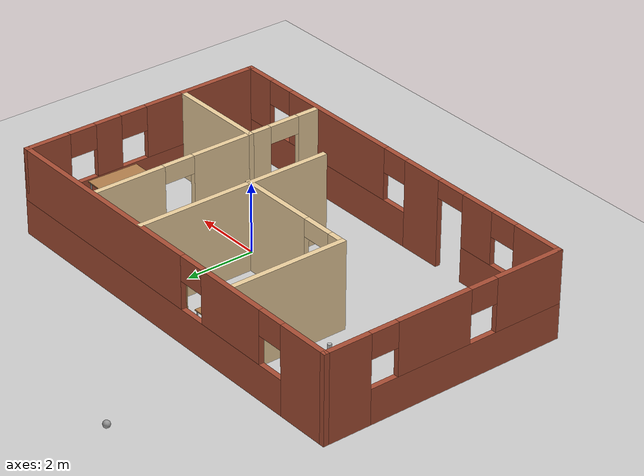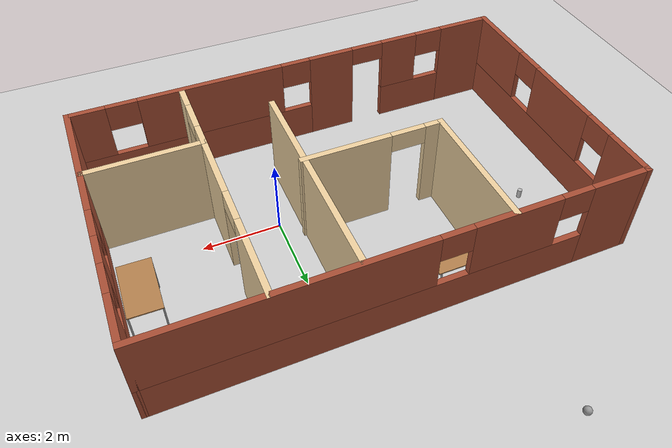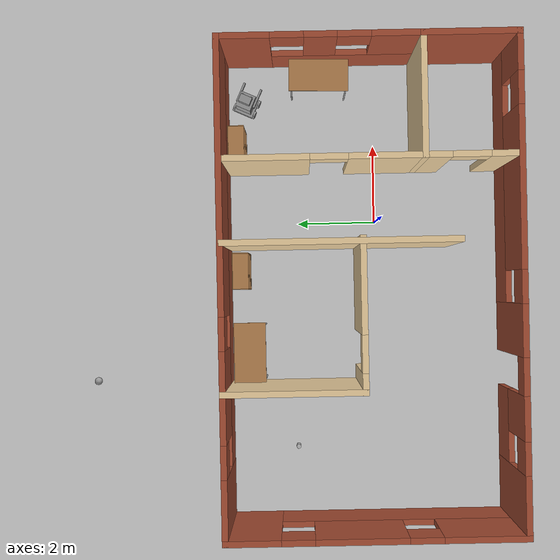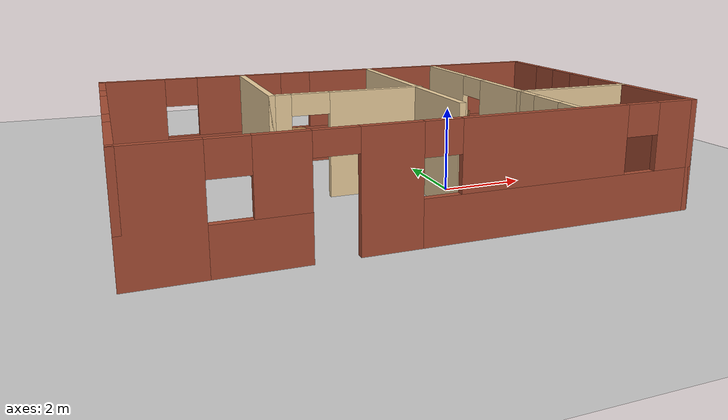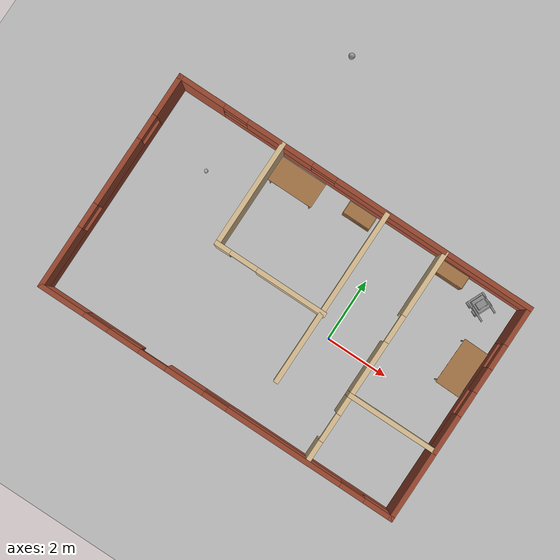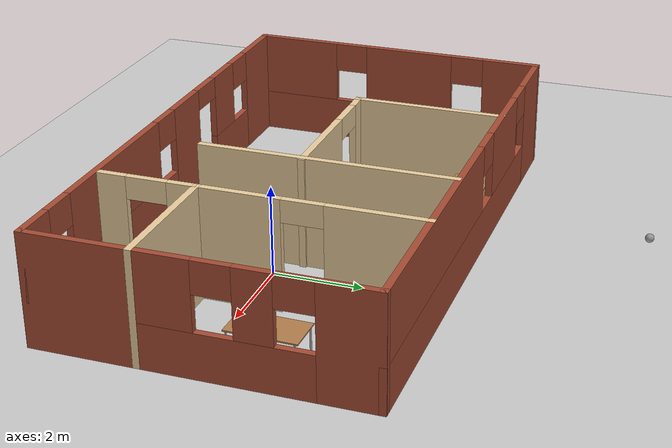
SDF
<sdf version="1.6">
 <world name="default">
  <plugin name="hello" filename="libhello.so"/>
  <light name="sun" type="directional">
   <pose>0 0 10 0 -0 0</pose>
   <diffuse>0.8 0.8 0.8 1</diffuse>
   <specular>0.2 0.2 0.2 1</specular>
   <attenuation>
    <range>1000</range>
    <constant>0.9</constant>
    <linear>0.01</linear>
    <quadratic>0.001</quadratic>
   </attenuation>
   <direction>-0.5 0.1 -0.9</direction>
   <spot><inner_angle>0</inner_angle><outer_angle>0</outer_angle><falloff>0</falloff></spot>
  </light>
  <model name="ground_plane">
   <static>1</static>
   <link name="link">
    <collision name="collision">
     <geometry><plane><normal>0 0 1</normal><size>100 100</size></plane></geometry>
     <surface>
      <contact><collide_bitmask>65535</collide_bitmask></contact>
      <friction><ode><mu>100</mu><mu2>50</mu2></ode></friction>
     </surface>
    </collision>
    <visual name="visual">
     <cast_shadows>0</cast_shadows>
     <geometry><plane><normal>0 0 1</normal><size>100 100</size></plane></geometry>
     <material>
      <script><uri>file://media/materials/scripts/gazebo.material</uri><name>Gazebo/Grey</name></script>
     </material>
    </visual>
   </link>
  </model>
  <gravity>0 0 -9.8</gravity>
  <magnetic_field>6e-06 2.3e-05 -4.2e-05</magnetic_field>
  <atmosphere type="adiabatic"/>
  <physics name="default_physics" default="0" type="ode">
   <max_step_size>0.001</max_step_size>
   <real_time_factor>1</real_time_factor>
   <real_time_update_rate>1000</real_time_update_rate>
  </physics>
  <scene><ambient>0.4 0.4 0.4 1</ambient><background>0.7 0.7 0.7 1</background><shadows>1</shadows></scene>
  <spherical_coordinates>
   <surface_model>EARTH_WGS84</surface_model>
   <latitude_deg>0</latitude_deg>
   <longitude_deg>0</longitude_deg>
   <elevation>0</elevation>
   <heading_deg>0</heading_deg>
  </spherical_coordinates>
  <model name="apartment">
   <pose>-1.69639 0.317076 0 0 -0 0</pose>
   <link name="Wall_10">
    <pose>-5.925 -0.028256 0 0 -0 -1.5708</pose>
    <visual name="Wall_10_Visual_0">
     <pose>-2.93317 0 1.25 0 -0 0</pose>
     <geometry><box><size>1.38366 0.15 2.5</size></box></geometry>
     <material>
      <script><uri>file://media/materials/scripts/gazebo.material</uri><name>Gazebo/Bricks</name></script>
      <ambient>1 1 1 1</ambient>
     </material>
     <meta><layer>0</layer></meta>
    </visual>
    <collision name="Wall_10_Collision_0">
     <geometry><box><size>1.38366 0.15 2.5</size></box></geometry>
     <pose>-2.93317 0 1.25 0 -0 0</pose>
    </collision>
    <visual name="Wall_10_Visual_1">
     <pose>0.691828 0 0.5 0 -0 0</pose>
     <geometry><box><size>5.86634 0.15 1</size></box></geometry>
     <material>
      <script><uri>file://media/materials/scripts/gazebo.material</uri><name>Gazebo/Bricks</name></script>
      <ambient>1 1 1 1</ambient>
     </material>
     <meta><layer>0</layer></meta>
    </visual>
    <collision name="Wall_10_Collision_1">
     <geometry><box><size>5.86634 0.15 1</size></box></geometry>
     <pose>0.691828 0 0.5 0 -0 0</pose>
    </collision>
    <visual name="Wall_10_Visual_2">
     <pose>-0.338336 0 1.75 0 -0 0</pose>
     <geometry><box><size>2.20601 0.15 1.5</size></box></geometry>
     <material>
      <script><uri>file://media/materials/scripts/gazebo.material</uri><name>Gazebo/Bricks</name></script>
      <ambient>1 1 1 1</ambient>
     </material>
     <meta><layer>0</layer></meta>
    </visual>
    <collision name="Wall_10_Collision_2">
     <geometry><box><size>2.20601 0.15 1.5</size></box></geometry>
     <pose>-0.338336 0 1.75 0 -0 0</pose>
    </collision>
    <visual name="Wall_10_Visual_3">
     <pose>2.59484 0 1.75 0 -0 0</pose>
     <geometry><box><size>2.06033 0.15 1.5</size></box></geometry>
     <material>
      <script><uri>file://media/materials/scripts/gazebo.material</uri><name>Gazebo/Bricks</name></script>
      <ambient>1 1 1 1</ambient>
     </material>
     <meta><layer>0</layer></meta>
    </visual>
    <collision name="Wall_10_Collision_3">
     <geometry><box><size>2.06033 0.15 1.5</size></box></geometry>
     <pose>2.59484 0 1.75 0 -0 0</pose>
    </collision>
    <visual name="Wall_10_Visual_4">
     <pose>-1.84134 0 2.15 0 -0 0</pose>
     <geometry><box><size>0.8 0.15 0.7</size></box></geometry>
     <material>
      <script><uri>file://media/materials/scripts/gazebo.material</uri><name>Gazebo/Bricks</name></script>
      <ambient>1 1 1 1</ambient>
     </material>
     <meta><layer>0</layer></meta>
    </visual>
    <collision name="Wall_10_Collision_4">
     <geometry><box><size>0.8 0.15 0.7</size></box></geometry>
     <pose>-1.84134 0 2.15 0 -0 0</pose>
    </collision>
    <visual name="Wall_10_Visual_5">
     <pose>1.16467 0 2.15 0 -0 0</pose>
     <geometry><box><size>0.8 0.15 0.7</size></box></geometry>
     <material>
      <script><uri>file://media/materials/scripts/gazebo.material</uri><name>Gazebo/Bricks</name></script>
      <ambient>1 1 1 1</ambient>
     </material>
     <meta><layer>0</layer></meta>
    </visual>
    <collision name="Wall_10_Collision_5">
     <geometry><box><size>0.8 0.15 0.7</size></box></geometry>
     <pose>1.16467 0 2.15 0 -0 0</pose>
    </collision>
   </link>
   <link name="Wall_11">
    <pose>-0 -3.57826 0 0 -0 0</pose>
    <visual name="Wall_11_Visual_0">
     <pose>-5.2325 0 1.25 0 -0 0</pose>
     <geometry><box><size>1.535 0.15 2.5</size></box></geometry>
     <material>
      <script><uri>file://media/materials/scripts/gazebo.material</uri><name>Gazebo/Bricks</name></script>
      <ambient>1 1 1 1</ambient>
     </material>
     <meta><layer>0</layer></meta>
    </visual>
    <collision name="Wall_11_Collision_0">
     <geometry><box><size>1.535 0.15 2.5</size></box></geometry>
     <pose>-5.2325 0 1.25 0 -0 0</pose>
    </collision>
    <visual name="Wall_11_Visual_1">
     <pose>-1.07324 0 1.25 0 -0 0</pose>
     <geometry><box><size>1.26192 0.15 2.5</size></box></geometry>
     <material>
      <script><uri>file://media/materials/scripts/gazebo.material</uri><name>Gazebo/Bricks</name></script>
      <ambient>1 1 1 1</ambient>
     </material>
     <meta><layer>0</layer></meta>
    </visual>
    <collision name="Wall_11_Collision_1">
     <geometry><box><size>1.26192 0.15 2.5</size></box></geometry>
     <pose>-1.07324 0 1.25 0 -0 0</pose>
    </collision>
    <visual name="Wall_11_Visual_2">
     <pose>-3.5346 0 0.5 0 -0 0</pose>
     <geometry><box><size>1.86079 0.15 1</size></box></geometry>
     <material>
      <script><uri>file://media/materials/scripts/gazebo.material</uri><name>Gazebo/Bricks</name></script>
      <ambient>1 1 1 1</ambient>
     </material>
     <meta><layer>0</layer></meta>
    </visual>
    <collision name="Wall_11_Collision_2">
     <geometry><box><size>1.86079 0.15 1</size></box></geometry>
     <pose>-3.5346 0 0.5 0 -0 0</pose>
    </collision>
    <visual name="Wall_11_Visual_3">
     <pose>2.77886 0 0.5 0 -0 0</pose>
     <geometry><box><size>6.44228 0.15 1</size></box></geometry>
     <material>
      <script><uri>file://media/materials/scripts/gazebo.material</uri><name>Gazebo/Bricks</name></script>
      <ambient>1 1 1 1</ambient>
     </material>
     <meta><layer>0</layer></meta>
    </visual>
    <collision name="Wall_11_Collision_3">
     <geometry><box><size>6.44228 0.15 1</size></box></geometry>
     <pose>2.77886 0 0.5 0 -0 0</pose>
    </collision>
    <visual name="Wall_11_Visual_4">
     <pose>-3.1346 0 1.75 0 -0 0</pose>
     <geometry><box><size>1.06079 0.15 1.5</size></box></geometry>
     <material>
      <script><uri>file://media/materials/scripts/gazebo.material</uri><name>Gazebo/Bricks</name></script>
      <ambient>1 1 1 1</ambient>
     </material>
     <meta><layer>0</layer></meta>
    </visual>
    <collision name="Wall_11_Collision_4">
     <geometry><box><size>1.06079 0.15 1.5</size></box></geometry>
     <pose>-3.1346 0 1.75 0 -0 0</pose>
    </collision>
    <visual name="Wall_11_Visual_5">
     <pose>-3.1346 0 1.75 0 -0 0</pose>
     <geometry><box><size>1.06079 0.15 1.5</size></box></geometry>
     <material>
      <script><uri>file://media/materials/scripts/gazebo.material</uri><name>Gazebo/Bricks</name></script>
      <ambient>1 1 1 1</ambient>
     </material>
     <meta><layer>0</layer></meta>
    </visual>
    <collision name="Wall_11_Collision_5">
     <geometry><box><size>1.06079 0.15 1.5</size></box></geometry>
     <pose>-3.1346 0 1.75 0 -0 0</pose>
    </collision>
    <visual name="Wall_11_Visual_6">
     <pose>2.28084 0 1.75 0 -0 0</pose>
     <geometry><box><size>3.84624 0.15 1.5</size></box></geometry>
     <material>
      <script><uri>file://media/materials/scripts/gazebo.material</uri><name>Gazebo/Bricks</name></script>
      <ambient>1 1 1 1</ambient>
     </material>
     <meta><layer>0</layer></meta>
    </visual>
    <collision name="Wall_11_Collision_6">
     <geometry><box><size>3.84624 0.15 1.5</size></box></geometry>
     <pose>2.28084 0 1.75 0 -0 0</pose>
    </collision>
    <visual name="Wall_11_Visual_7">
     <pose>5.50198 0 1.75 0 -0 0</pose>
     <geometry><box><size>0.996046 0.15 1.5</size></box></geometry>
     <material>
      <script><uri>file://media/materials/scripts/gazebo.material</uri><name>Gazebo/Bricks</name></script>
      <ambient>1 1 1 1</ambient>
     </material>
     <meta><layer>0</layer></meta>
    </visual>
    <collision name="Wall_11_Collision_7">
     <geometry><box><size>0.996046 0.15 1.5</size></box></geometry>
     <pose>5.50198 0 1.75 0 -0 0</pose>
    </collision>
    <visual name="Wall_11_Visual_8">
     <pose>-4.065 0 2.15 0 -0 0</pose>
     <geometry><box><size>0.8 0.15 0.7</size></box></geometry>
     <material>
      <script><uri>file://media/materials/scripts/gazebo.material</uri><name>Gazebo/Bricks</name></script>
      <ambient>1 1 1 1</ambient>
     </material>
     <meta><layer>0</layer></meta>
    </visual>
    <collision name="Wall_11_Collision_8">
     <geometry><box><size>0.8 0.15 0.7</size></box></geometry>
     <pose>-4.065 0 2.15 0 -0 0</pose>
    </collision>
    <visual name="Wall_11_Visual_9">
     <pose>-0.042282 0 2.15 0 -0 0</pose>
     <geometry><box><size>0.8 0.15 0.7</size></box></geometry>
     <material>
      <script><uri>file://media/materials/scripts/gazebo.material</uri><name>Gazebo/Bricks</name></script>
      <ambient>1 1 1 1</ambient>
     </material>
     <meta><layer>0</layer></meta>
    </visual>
    <collision name="Wall_11_Collision_9">
     <geometry><box><size>0.8 0.15 0.7</size></box></geometry>
     <pose>-0.042282 0 2.15 0 -0 0</pose>
    </collision>
    <visual name="Wall_11_Visual_10">
     <pose>4.60395 0 2.15 0 -0 0</pose>
     <geometry><box><size>0.8 0.15 0.7</size></box></geometry>
     <material>
      <script><uri>file://media/materials/scripts/gazebo.material</uri><name>Gazebo/Bricks</name></script>
      <ambient>1 1 1 1</ambient>
     </material>
     <meta><layer>0</layer></meta>
    </visual>
    <collision name="Wall_11_Collision_10">
     <geometry><box><size>0.8 0.15 0.7</size></box></geometry>
     <pose>4.60395 0 2.15 0 -0 0</pose>
    </collision>
    <visual name="Wall_11_Visual_11">
     <pose>-2.15421 0 2.25 0 -0 0</pose>
     <geometry><box><size>0.9 0.15 0.5</size></box></geometry>
     <material>
      <script><uri>file://media/materials/scripts/gazebo.material</uri><name>Gazebo/Bricks</name></script>
      <ambient>1 1 1 1</ambient>
     </material>
     <meta><layer>0</layer></meta>
    </visual>
    <collision name="Wall_11_Collision_11">
     <geometry><box><size>0.9 0.15 0.5</size></box></geometry>
     <pose>-2.15421 0 2.25 0 -0 0</pose>
    </collision>
    <visual name="Wall_11_Visual_12">
     <pose>-2.15421 0 2.25 0 -0 0</pose>
     <geometry><box><size>0.9 0.15 0.5</size></box></geometry>
     <material>
      <script><uri>file://media/materials/scripts/gazebo.material</uri><name>Gazebo/Bricks</name></script>
      <ambient>1 1 1 1</ambient>
     </material>
     <meta><layer>0</layer></meta>
    </visual>
    <collision name="Wall_11_Collision_12">
     <geometry><box><size>0.9 0.15 0.5</size></box></geometry>
     <pose>-2.15421 0 2.25 0 -0 0</pose>
    </collision>
   </link>
   <link name="Wall_12">
    <collision name="Wall_12_Collision">
     <geometry><box><size>2.4 0.15 2.5</size></box></geometry>
     <pose>0 0 1.25 0 -0 0</pose>
    </collision>
    <visual name="Wall_12_Visual">
     <pose>0 0 1.25 0 -0 0</pose>
     <geometry><box><size>2.4 0.15 2.5</size></box></geometry>
     <material>
      <script><uri>file://media/materials/scripts/gazebo.material</uri><name>Gazebo/Bricks</name></script>
      <ambient>1 1 1 1</ambient>
     </material>
     <meta><layer>0</layer></meta>
    </visual>
    <pose>5.925 -2.45326 0 0 -0 1.5708</pose>
   </link>
   <link name="Wall_14">
    <collision name="Wall_14_Collision">
     <geometry><box><size>5.75 0.15 2.5</size></box></geometry>
     <pose>0 0 1.25 0 -0 0</pose>
    </collision>
    <visual name="Wall_14_Visual">
     <pose>0 0 1.25 0 -0 0</pose>
     <geometry><box><size>5.75 0.15 2.5</size></box></geometry>
     <material>
      <script><uri>file://media/materials/scripts/gazebo.material</uri><name>Gazebo/Grey</name></script>
      <ambient>0.921569 0.807843 0.615686 1</ambient>
     </material>
     <meta><layer>0</layer></meta>
    </visual>
    <pose>1.10155 0.680987 0 0 -0 -1.5708</pose>
   </link>
   <link name="Wall_21">
    <collision name="Wall_21_Collision">
     <geometry><box><size>3.5 0.15 2.5</size></box></geometry>
     <pose>0 0 1.25 0 -0 0</pose>
    </collision>
    <visual name="Wall_21_Visual">
     <pose>0 0 1.25 0 -0 0</pose>
     <geometry><box><size>3.5 0.15 2.5</size></box></geometry>
     <material>
      <script><uri>file://media/materials/scripts/gazebo.material</uri><name>Gazebo/Grey</name></script>
      <ambient>0.921569 0.807843 0.615686 1</ambient>
     </material>
     <meta><layer>0</layer></meta>
    </visual>
    <pose>-2.44698 1.84407 0 0 -0 -1.5708</pose>
   </link>
   <link name="Wall_22">
    <pose>-0.646975 0.169069 0 0 -0 0</pose>
    <visual name="Wall_22_Visual_0">
     <pose>-1.61441 0 1.25 0 -0 0</pose>
     <geometry><box><size>0.521175 0.15 2.5</size></box></geometry>
     <material>
      <script><uri>file://media/materials/scripts/gazebo.material</uri><name>Gazebo/Grey</name></script>
      <ambient>0.921569 0.807843 0.615686 1</ambient>
     </material>
     <meta><layer>0</layer></meta>
    </visual>
    <collision name="Wall_22_Collision_0">
     <geometry><box><size>0.521175 0.15 2.5</size></box></geometry>
     <pose>-1.61441 0 1.25 0 -0 0</pose>
    </collision>
    <visual name="Wall_22_Visual_1">
     <pose>0.710588 0 1.25 0 -0 0</pose>
     <geometry><box><size>2.32883 0.15 2.5</size></box></geometry>
     <material>
      <script><uri>file://media/materials/scripts/gazebo.material</uri><name>Gazebo/Grey</name></script>
      <ambient>0.921569 0.807843 0.615686 1</ambient>
     </material>
     <meta><layer>0</layer></meta>
    </visual>
    <collision name="Wall_22_Collision_1">
     <geometry><box><size>2.32883 0.15 2.5</size></box></geometry>
     <pose>0.710588 0 1.25 0 -0 0</pose>
    </collision>
    <visual name="Wall_22_Visual_2">
     <pose>-0.903825 0 2.25 0 -0 0</pose>
     <geometry><box><size>0.9 0.15 0.5</size></box></geometry>
     <material>
      <script><uri>file://media/materials/scripts/gazebo.material</uri><name>Gazebo/Grey</name></script>
      <ambient>0.921569 0.807843 0.615686 1</ambient>
     </material>
     <meta><layer>0</layer></meta>
    </visual>
    <collision name="Wall_22_Collision_2">
     <geometry><box><size>0.9 0.15 0.5</size></box></geometry>
     <pose>-0.903825 0 2.25 0 -0 0</pose>
    </collision>
   </link>
   <link name="Wall_24">
    <pose>3.075 -2.37826 0 0 -0 -1.5708</pose>
    <visual name="Wall_24_Visual_0">
     <pose>-0.771247 0 1.25 0 -0 0</pose>
     <geometry><box><size>0.707506 0.15 2.5</size></box></geometry>
     <material>
      <script><uri>file://media/materials/scripts/gazebo.material</uri><name>Gazebo/Grey</name></script>
      <ambient>0.921569 0.807843 0.615686 1</ambient>
     </material>
     <meta><layer>0</layer></meta>
    </visual>
    <collision name="Wall_24_Collision_0">
     <geometry><box><size>0.707506 0.15 2.5</size></box></geometry>
     <pose>-0.771247 0 1.25 0 -0 0</pose>
    </collision>
    <visual name="Wall_24_Visual_1">
     <pose>0.803753 0 1.25 0 -0 0</pose>
     <geometry><box><size>0.642494 0.15 2.5</size></box></geometry>
     <material>
      <script><uri>file://media/materials/scripts/gazebo.material</uri><name>Gazebo/Grey</name></script>
      <ambient>0.921569 0.807843 0.615686 1</ambient>
     </material>
     <meta><layer>0</layer></meta>
    </visual>
    <collision name="Wall_24_Collision_1">
     <geometry><box><size>0.642494 0.15 2.5</size></box></geometry>
     <pose>0.803753 0 1.25 0 -0 0</pose>
    </collision>
    <visual name="Wall_24_Visual_2">
     <pose>0.032506 0 2.25 0 -0 0</pose>
     <geometry><box><size>0.9 0.15 0.5</size></box></geometry>
     <material>
      <script><uri>file://media/materials/scripts/gazebo.material</uri><name>Gazebo/Grey</name></script>
      <ambient>0.921569 0.807843 0.615686 1</ambient>
     </material>
     <meta><layer>0</layer></meta>
    </visual>
    <collision name="Wall_24_Collision_2">
     <geometry><box><size>0.9 0.15 0.5</size></box></geometry>
     <pose>0.032506 0 2.25 0 -0 0</pose>
    </collision>
   </link>
   <link name="Wall_5">
    <pose>-0 3.52174 0 0 -0 0</pose>
    <visual name="Wall_5_Visual_0">
     <pose>-5.21398 0 1.25 0 -0 0</pose>
     <geometry><box><size>1.57204 0.15 2.5</size></box></geometry>
     <material>
      <script><uri>file://media/materials/scripts/gazebo.material</uri><name>Gazebo/Bricks</name></script>
      <ambient>1 1 1 1</ambient>
     </material>
     <meta><layer>0</layer></meta>
    </visual>
    <collision name="Wall_5_Collision_0">
     <geometry><box><size>1.57204 0.15 2.5</size></box></geometry>
     <pose>-5.21398 0 1.25 0 -0 0</pose>
    </collision>
    <visual name="Wall_5_Visual_1">
     <pose>0.78602 0 0.5 0 -0 0</pose>
     <geometry><box><size>10.428 0.15 1</size></box></geometry>
     <material>
      <script><uri>file://media/materials/scripts/gazebo.material</uri><name>Gazebo/Bricks</name></script>
      <ambient>1 1 1 1</ambient>
     </material>
     <meta><layer>0</layer></meta>
    </visual>
    <collision name="Wall_5_Collision_1">
     <geometry><box><size>10.428 0.15 1</size></box></geometry>
     <pose>0.78602 0 0.5 0 -0 0</pose>
    </collision>
    <visual name="Wall_5_Visual_2">
     <pose>-2.5279 0 1.75 0 -0 0</pose>
     <geometry><box><size>2.20011 0.15 1.5</size></box></geometry>
     <material>
      <script><uri>file://media/materials/scripts/gazebo.material</uri><name>Gazebo/Bricks</name></script>
      <ambient>1 1 1 1</ambient>
     </material>
     <meta><layer>0</layer></meta>
    </visual>
    <collision name="Wall_5_Collision_2">
     <geometry><box><size>2.20011 0.15 1.5</size></box></geometry>
     <pose>-2.5279 0 1.75 0 -0 0</pose>
    </collision>
    <visual name="Wall_5_Visual_3">
     <pose>2.68608 0 1.75 0 -0 0</pose>
     <geometry><box><size>6.62785 0.15 1.5</size></box></geometry>
     <material>
      <script><uri>file://media/materials/scripts/gazebo.material</uri><name>Gazebo/Bricks</name></script>
      <ambient>1 1 1 1</ambient>
     </material>
     <meta><layer>0</layer></meta>
    </visual>
    <collision name="Wall_5_Collision_3">
     <geometry><box><size>6.62785 0.15 1.5</size></box></geometry>
     <pose>2.68608 0 1.75 0 -0 0</pose>
    </collision>
    <visual name="Wall_5_Visual_4">
     <pose>-4.02796 0 2.15 0 -0 0</pose>
     <geometry><box><size>0.8 0.15 0.7</size></box></geometry>
     <material>
      <script><uri>file://media/materials/scripts/gazebo.material</uri><name>Gazebo/Bricks</name></script>
      <ambient>1 1 1 1</ambient>
     </material>
     <meta><layer>0</layer></meta>
    </visual>
    <collision name="Wall_5_Collision_4">
     <geometry><box><size>0.8 0.15 0.7</size></box></geometry>
     <pose>-4.02796 0 2.15 0 -0 0</pose>
    </collision>
    <visual name="Wall_5_Visual_5">
     <pose>-1.02785 0 2.15 0 -0 0</pose>
     <geometry><box><size>0.8 0.15 0.7</size></box></geometry>
     <material>
      <script><uri>file://media/materials/scripts/gazebo.material</uri><name>Gazebo/Bricks</name></script>
      <ambient>1 1 1 1</ambient>
     </material>
     <meta><layer>0</layer></meta>
    </visual>
    <collision name="Wall_5_Collision_5">
     <geometry><box><size>0.8 0.15 0.7</size></box></geometry>
     <pose>-1.02785 0 2.15 0 -0 0</pose>
    </collision>
   </link>
   <link name="Wall_6">
    <pose>5.925 1.09674 0 0 -0 -1.5708</pose>
    <visual name="Wall_6_Visual_0">
     <pose>-1.83834 0 1.25 0 -0 0</pose>
     <geometry><box><size>1.32332 0.15 2.5</size></box></geometry>
     <material>
      <script><uri>file://media/materials/scripts/gazebo.material</uri><name>Gazebo/Bricks</name></script>
      <ambient>1 1 1 1</ambient>
     </material>
     <meta><layer>0</layer></meta>
    </visual>
    <collision name="Wall_6_Collision_0">
     <geometry><box><size>1.32332 0.15 2.5</size></box></geometry>
     <pose>-1.83834 0 1.25 0 -0 0</pose>
    </collision>
    <visual name="Wall_6_Visual_1">
     <pose>0.661658 0 0.5 0 -0 0</pose>
     <geometry><box><size>3.67668 0.15 1</size></box></geometry>
     <material>
      <script><uri>file://media/materials/scripts/gazebo.material</uri><name>Gazebo/Bricks</name></script>
      <ambient>1 1 1 1</ambient>
     </material>
     <meta><layer>0</layer></meta>
    </visual>
    <collision name="Wall_6_Collision_1">
     <geometry><box><size>3.67668 0.15 1</size></box></geometry>
     <pose>0.661658 0 0.5 0 -0 0</pose>
    </collision>
    <visual name="Wall_6_Visual_2">
     <pose>0.017802 0 1.75 0 -0 0</pose>
     <geometry><box><size>0.788972 0.15 1.5</size></box></geometry>
     <material>
      <script><uri>file://media/materials/scripts/gazebo.material</uri><name>Gazebo/Bricks</name></script>
      <ambient>1 1 1 1</ambient>
     </material>
     <meta><layer>0</layer></meta>
    </visual>
    <collision name="Wall_6_Collision_2">
     <geometry><box><size>0.788972 0.15 1.5</size></box></geometry>
     <pose>0.017802 0 1.75 0 -0 0</pose>
    </collision>
    <visual name="Wall_6_Visual_3">
     <pose>1.85614 0 1.75 0 -0 0</pose>
     <geometry><box><size>1.28771 0.15 1.5</size></box></geometry>
     <material>
      <script><uri>file://media/materials/scripts/gazebo.material</uri><name>Gazebo/Bricks</name></script>
      <ambient>1 1 1 1</ambient>
     </material>
     <meta><layer>0</layer></meta>
    </visual>
    <collision name="Wall_6_Collision_3">
     <geometry><box><size>1.28771 0.15 1.5</size></box></geometry>
     <pose>1.85614 0 1.75 0 -0 0</pose>
    </collision>
    <visual name="Wall_6_Visual_4">
     <pose>-0.776684 0 2.15 0 -0 0</pose>
     <geometry><box><size>0.8 0.15 0.7</size></box></geometry>
     <material>
      <script><uri>file://media/materials/scripts/gazebo.material</uri><name>Gazebo/Bricks</name></script>
      <ambient>1 1 1 1</ambient>
     </material>
     <meta><layer>0</layer></meta>
    </visual>
    <collision name="Wall_6_Collision_4">
     <geometry><box><size>0.8 0.15 0.7</size></box></geometry>
     <pose>-0.776684 0 2.15 0 -0 0</pose>
    </collision>
    <visual name="Wall_6_Visual_5">
     <pose>0.812288 0 2.15 0 -0 0</pose>
     <geometry><box><size>0.8 0.15 0.7</size></box></geometry>
     <material>
      <script><uri>file://media/materials/scripts/gazebo.material</uri><name>Gazebo/Bricks</name></script>
      <ambient>1 1 1 1</ambient>
     </material>
     <meta><layer>0</layer></meta>
    </visual>
    <collision name="Wall_6_Collision_5">
     <geometry><box><size>0.8 0.15 0.7</size></box></geometry>
     <pose>0.812288 0 2.15 0 -0 0</pose>
    </collision>
   </link>
   <link name="Wall_7">
    <collision name="Wall_7_Collision">
     <geometry><box><size>3 0.15 2.5</size></box></geometry>
     <pose>0 0 1.25 0 -0 0</pose>
    </collision>
    <visual name="Wall_7_Visual">
     <pose>0 0 1.25 0 -0 0</pose>
     <geometry><box><size>3 0.15 2.5</size></box></geometry>
     <material>
      <script><uri>file://media/materials/scripts/gazebo.material</uri><name>Gazebo/Grey</name></script>
      <ambient>0.921569 0.807843 0.615686 1</ambient>
     </material>
     <meta><layer>0</layer></meta>
    </visual>
    <pose>4.5 -1.32826 0 0 -0 3.14159</pose>
   </link>
   <link name="Wall_8">
    <pose>3.075 1.09674 0 0 -0 1.5708</pose>
    <visual name="Wall_8_Visual_0">
     <pose>-1.55933 0 1.25 0 -0 0</pose>
     <geometry><box><size>1.88135 0.15 2.5</size></box></geometry>
     <material>
      <script><uri>file://media/materials/scripts/gazebo.material</uri><name>Gazebo/Grey</name></script>
      <ambient>0.921569 0.807843 0.615686 1</ambient>
     </material>
     <meta><layer>0</layer></meta>
    </visual>
    <collision name="Wall_8_Collision_0">
     <geometry><box><size>1.88135 0.15 2.5</size></box></geometry>
     <pose>-1.55933 0 1.25 0 -0 0</pose>
    </collision>
    <visual name="Wall_8_Visual_1">
     <pose>1.39067 0 1.25 0 -0 0</pose>
     <geometry><box><size>2.21865 0.15 2.5</size></box></geometry>
     <material>
      <script><uri>file://media/materials/scripts/gazebo.material</uri><name>Gazebo/Grey</name></script>
      <ambient>0.921569 0.807843 0.615686 1</ambient>
     </material>
     <meta><layer>0</layer></meta>
    </visual>
    <collision name="Wall_8_Collision_1">
     <geometry><box><size>2.21865 0.15 2.5</size></box></geometry>
     <pose>1.39067 0 1.25 0 -0 0</pose>
    </collision>
    <visual name="Wall_8_Visual_2">
     <pose>-0.168653 0 2.25 0 -0 0</pose>
     <geometry><box><size>0.9 0.15 0.5</size></box></geometry>
     <material>
      <script><uri>file://media/materials/scripts/gazebo.material</uri><name>Gazebo/Grey</name></script>
      <ambient>0.921569 0.807843 0.615686 1</ambient>
     </material>
     <meta><layer>0</layer></meta>
    </visual>
    <collision name="Wall_8_Collision_2">
     <geometry><box><size>0.9 0.15 0.5</size></box></geometry>
     <pose>-0.168653 0 2.25 0 -0 0</pose>
    </collision>
   </link>
   <static>1</static>
  </model>
  <model name="bookshelf">
   <static>1</static>
   <link name="link">
    <inertial><mass>1</mass></inertial>
    <collision name="back">
     <pose>0 0.005 0.6 0 -0 0</pose>
     <geometry><box><size>0.9 0.01 1.2</size></box></geometry>
    </collision>
    <visual name="visual1">
     <pose>0 0.005 0.6 0 -0 0</pose>
     <geometry><box><size>0.9 0.01 1.2</size></box></geometry>
     <material>
      <script><uri>file://media/materials/scripts/gazebo.material</uri><name>Gazebo/Wood</name></script>
     </material>
    </visual>
    <collision name="left_side">
     <pose>0.45 -0.195 0.6 0 -0 0</pose>
     <geometry><box><size>0.02 0.4 1.2</size></box></geometry>
    </collision>
    <visual name="visual2">
     <pose>0.45 -0.195 0.6 0 -0 0</pose>
     <geometry><box><size>0.02 0.4 1.2</size></box></geometry>
     <material>
      <script><uri>file://media/materials/scripts/gazebo.material</uri><name>Gazebo/Wood</name></script>
     </material>
    </visual>
    <collision name="right_side">
     <pose>-0.45 -0.195 0.6 0 -0 0</pose>
     <geometry><box><size>0.02 0.4 1.2</size></box></geometry>
    </collision>
    <visual name="visual3">
     <pose>-0.45 -0.195 0.6 0 -0 0</pose>
     <geometry><box><size>0.02 0.4 1.2</size></box></geometry>
     <material>
      <script><uri>file://media/materials/scripts/gazebo.material</uri><name>Gazebo/Wood</name></script>
     </material>
    </visual>
    <collision name="bottom">
     <pose>0 -0.195 0.03 0 -0 0</pose>
     <geometry><box><size>0.88 0.4 0.06</size></box></geometry>
    </collision>
    <visual name="visual4">
     <pose>0 -0.195 0.03 0 -0 0</pose>
     <geometry><box><size>0.88 0.4 0.06</size></box></geometry>
     <material>
      <script><uri>file://media/materials/scripts/gazebo.material</uri><name>Gazebo/Wood</name></script>
     </material>
    </visual>
    <collision name="top">
     <pose>0 -0.195 1.19 0 -0 0</pose>
     <geometry><box><size>0.88 0.4 0.02</size></box></geometry>
    </collision>
    <visual name="visual5">
     <pose>0 -0.195 1.19 0 -0 0</pose>
     <geometry><box><size>0.88 0.4 0.02</size></box></geometry>
     <material>
      <script><uri>file://media/materials/scripts/gazebo.material</uri><name>Gazebo/Wood</name></script>
     </material>
    </visual>
    <collision name="low_shelf">
     <pose>0 -0.195 0.43 0 -0 0</pose>
     <geometry><box><size>0.88 0.4 0.02</size></box></geometry>
    </collision>
    <visual name="visual6">
     <pose>0 -0.195 0.43 0 -0 0</pose>
     <geometry><box><size>0.88 0.4 0.02</size></box></geometry>
     <material>
      <script><uri>file://media/materials/scripts/gazebo.material</uri><name>Gazebo/Wood</name></script>
     </material>
    </visual>
    <collision name="high_shelf">
     <pose>0 -0.195 0.8 0 -0 0</pose>
     <geometry><box><size>0.88 0.4 0.02</size></box></geometry>
    </collision>
    <visual name="visual7">
     <pose>0 -0.195 0.8 0 -0 0</pose>
     <geometry><box><size>0.88 0.4 0.02</size></box></geometry>
     <material>
      <script><uri>file://media/materials/scripts/gazebo.material</uri><name>Gazebo/Wood</name></script>
     </material>
    </visual>
   </link>
   <pose>-1.23153 3.65908 0 0 -0 0</pose>
  </model>
  <model name="bookshelf_0">
   <static>1</static>
   <link name="link">
    <inertial><mass>1</mass></inertial>
    <collision name="back">
     <pose>0 0.005 0.6 0 -0 0</pose>
     <geometry><box><size>0.9 0.01 1.2</size></box></geometry>
    </collision>
    <visual name="visual1">
     <pose>0 0.005 0.6 0 -0 0</pose>
     <geometry><box><size>0.9 0.01 1.2</size></box></geometry>
     <material>
      <script><uri>file://media/materials/scripts/gazebo.material</uri><name>Gazebo/Wood</name></script>
     </material>
    </visual>
    <collision name="left_side">
     <pose>0.45 -0.195 0.6 0 -0 0</pose>
     <geometry><box><size>0.02 0.4 1.2</size></box></geometry>
    </collision>
    <visual name="visual2">
     <pose>0.45 -0.195 0.6 0 -0 0</pose>
     <geometry><box><size>0.02 0.4 1.2</size></box></geometry>
     <material>
      <script><uri>file://media/materials/scripts/gazebo.material</uri><name>Gazebo/Wood</name></script>
     </material>
    </visual>
    <collision name="right_side">
     <pose>-0.45 -0.195 0.6 0 -0 0</pose>
     <geometry><box><size>0.02 0.4 1.2</size></box></geometry>
    </collision>
    <visual name="visual3">
     <pose>-0.45 -0.195 0.6 0 -0 0</pose>
     <geometry><box><size>0.02 0.4 1.2</size></box></geometry>
     <material>
      <script><uri>file://media/materials/scripts/gazebo.material</uri><name>Gazebo/Wood</name></script>
     </material>
    </visual>
    <collision name="bottom">
     <pose>0 -0.195 0.03 0 -0 0</pose>
     <geometry><box><size>0.88 0.4 0.06</size></box></geometry>
    </collision>
    <visual name="visual4">
     <pose>0 -0.195 0.03 0 -0 0</pose>
     <geometry><box><size>0.88 0.4 0.06</size></box></geometry>
     <material>
      <script><uri>file://media/materials/scripts/gazebo.material</uri><name>Gazebo/Wood</name></script>
     </material>
    </visual>
    <collision name="top">
     <pose>0 -0.195 1.19 0 -0 0</pose>
     <geometry><box><size>0.88 0.4 0.02</size></box></geometry>
    </collision>
    <visual name="visual5">
     <pose>0 -0.195 1.19 0 -0 0</pose>
     <geometry><box><size>0.88 0.4 0.02</size></box></geometry>
     <material>
      <script><uri>file://media/materials/scripts/gazebo.material</uri><name>Gazebo/Wood</name></script>
     </material>
    </visual>
    <collision name="low_shelf">
     <pose>0 -0.195 0.43 0 -0 0</pose>
     <geometry><box><size>0.88 0.4 0.02</size></box></geometry>
    </collision>
    <visual name="visual6">
     <pose>0 -0.195 0.43 0 -0 0</pose>
     <geometry><box><size>0.88 0.4 0.02</size></box></geometry>
     <material>
      <script><uri>file://media/materials/scripts/gazebo.material</uri><name>Gazebo/Wood</name></script>
     </material>
    </visual>
    <collision name="high_shelf">
     <pose>0 -0.195 0.8 0 -0 0</pose>
     <geometry><box><size>0.88 0.4 0.02</size></box></geometry>
    </collision>
    <visual name="visual7">
     <pose>0 -0.195 0.8 0 -0 0</pose>
     <geometry><box><size>0.88 0.4 0.02</size></box></geometry>
     <material>
      <script><uri>file://media/materials/scripts/gazebo.material</uri><name>Gazebo/Wood</name></script>
     </material>
    </visual>
   </link>
   <pose>1.93792 3.70961 0 0 -0 0</pose>
  </model>
  <model name="beer">
   <link name="link">
    <pose>0 0 0.115 0 -0 0</pose>
    <inertial>
     <mass>0.39</mass>
     <inertia><ixx>0.00058</ixx><ixy>0</ixy><ixz>0</ixz><iyy>0.00058</iyy><iyz>0</iyz><izz>0.00019</izz></inertia>
    </inertial>
    <collision name="collision">
     <geometry><cylinder><radius>0.055</radius><length>0.23</length></cylinder></geometry>
    </collision>
    <visual name="visual">
     <geometry><cylinder><radius>0.055</radius><length>0.23</length></cylinder></geometry>
     <material>
      <script>
       <uri>model://beer/materials/scripts</uri>
       <uri>model://beer/materials/textures</uri>
       <name>Beer/Diffuse</name>
      </script>
     </material>
    </visual>
   </link>
   <pose>-5.657 2.08617 0.775001 -1e-06 2.6e-05 0.002773</pose>
  </model>
  <model name="table">
   <static>1</static>
   <link name="link">
    <collision name="surface">
     <pose>0 0 1 0 -0 0</pose>
     <geometry><box><size>1.5 0.8 0.03</size></box></geometry>
     <surface><friction><ode><mu>0.6</mu><mu2>0.6</mu2></ode></friction></surface>
    </collision>
    <visual name="visual1">
     <pose>0 0 1 0 -0 0</pose>
     <geometry><box><size>1.5 0.8 0.03</size></box></geometry>
     <material>
      <script><uri>file://media/materials/scripts/gazebo.material</uri><name>Gazebo/Wood</name></script>
     </material>
    </visual>
    <collision name="front_left_leg">
     <pose>0.68 0.38 0.5 0 -0 0</pose>
     <geometry><cylinder><radius>0.02</radius><length>1</length></cylinder></geometry>
    </collision>
    <visual name="front_left_leg">
     <pose>0.68 0.38 0.5 0 -0 0</pose>
     <geometry><cylinder><radius>0.02</radius><length>1</length></cylinder></geometry>
     <material>
      <script><uri>file://media/materials/scripts/gazebo.material</uri><name>Gazebo/Grey</name></script>
     </material>
    </visual>
    <collision name="front_right_leg">
     <pose>0.68 -0.38 0.5 0 -0 0</pose>
     <geometry><cylinder><radius>0.02</radius><length>1</length></cylinder></geometry>
    </collision>
    <visual name="front_right_leg">
     <pose>0.68 -0.38 0.5 0 -0 0</pose>
     <geometry><cylinder><radius>0.02</radius><length>1</length></cylinder></geometry>
     <material>
      <script><uri>file://media/materials/scripts/gazebo.material</uri><name>Gazebo/Grey</name></script>
     </material>
    </visual>
    <collision name="back_right_leg">
     <pose>-0.68 -0.38 0.5 0 -0 0</pose>
     <geometry><cylinder><radius>0.02</radius><length>1</length></cylinder></geometry>
    </collision>
    <visual name="back_right_leg">
     <pose>-0.68 -0.38 0.5 0 -0 0</pose>
     <geometry><cylinder><radius>0.02</radius><length>1</length></cylinder></geometry>
     <material>
      <script><uri>file://media/materials/scripts/gazebo.material</uri><name>Gazebo/Grey</name></script>
     </material>
    </visual>
    <collision name="back_left_leg">
     <pose>-0.68 0.38 0.5 0 -0 0</pose>
     <geometry><cylinder><radius>0.02</radius><length>1</length></cylinder></geometry>
    </collision>
    <visual name="back_left_leg">
     <pose>-0.68 0.38 0.5 0 -0 0</pose>
     <geometry><cylinder><radius>0.02</radius><length>1</length></cylinder></geometry>
     <material>
      <script><uri>file://media/materials/scripts/gazebo.material</uri><name>Gazebo/Grey</name></script>
     </material>
    </visual>
   </link>
   <pose>3.65777 1.42031 0.001054 -0.004408 -9.2e-05 -1.59161</pose>
  </model>
  <model name="table_0">
   <static>1</static>
   <link name="link">
    <collision name="surface">
     <pose>0 0 1 0 -0 0</pose>
     <geometry><box><size>1.5 0.8 0.03</size></box></geometry>
     <surface><friction><ode><mu>0.6</mu><mu2>0.6</mu2></ode></friction></surface>
    </collision>
    <visual name="visual1">
     <pose>0 0 1 0 -0 0</pose>
     <geometry><box><size>1.5 0.8 0.03</size></box></geometry>
     <material>
      <script><uri>file://media/materials/scripts/gazebo.material</uri><name>Gazebo/Wood</name></script>
     </material>
    </visual>
    <collision name="front_left_leg">
     <pose>0.68 0.38 0.5 0 -0 0</pose>
     <geometry><cylinder><radius>0.02</radius><length>1</length></cylinder></geometry>
    </collision>
    <visual name="front_left_leg">
     <pose>0.68 0.38 0.5 0 -0 0</pose>
     <geometry><cylinder><radius>0.02</radius><length>1</length></cylinder></geometry>
     <material>
      <script><uri>file://media/materials/scripts/gazebo.material</uri><name>Gazebo/Grey</name></script>
     </material>
    </visual>
    <collision name="front_right_leg">
     <pose>0.68 -0.38 0.5 0 -0 0</pose>
     <geometry><cylinder><radius>0.02</radius><length>1</length></cylinder></geometry>
    </collision>
    <visual name="front_right_leg">
     <pose>0.68 -0.38 0.5 0 -0 0</pose>
     <geometry><cylinder><radius>0.02</radius><length>1</length></cylinder></geometry>
     <material>
      <script><uri>file://media/materials/scripts/gazebo.material</uri><name>Gazebo/Grey</name></script>
     </material>
    </visual>
    <collision name="back_right_leg">
     <pose>-0.68 -0.38 0.5 0 -0 0</pose>
     <geometry><cylinder><radius>0.02</radius><length>1</length></cylinder></geometry>
    </collision>
    <visual name="back_right_leg">
     <pose>-0.68 -0.38 0.5 0 -0 0</pose>
     <geometry><cylinder><radius>0.02</radius><length>1</length></cylinder></geometry>
     <material>
      <script><uri>file://media/materials/scripts/gazebo.material</uri><name>Gazebo/Grey</name></script>
     </material>
    </visual>
    <collision name="back_left_leg">
     <pose>-0.68 0.38 0.5 0 -0 0</pose>
     <geometry><cylinder><radius>0.02</radius><length>1</length></cylinder></geometry>
    </collision>
    <visual name="back_left_leg">
     <pose>-0.68 0.38 0.5 0 -0 0</pose>
     <geometry><cylinder><radius>0.02</radius><length>1</length></cylinder></geometry>
     <material>
      <script><uri>file://media/materials/scripts/gazebo.material</uri><name>Gazebo/Grey</name></script>
     </material>
    </visual>
   </link>
   <pose>-3.28018 3.26918 0 0 -0 0</pose>
  </model>
  <model name="white_ball">
   <link name="link">
    <inertial>
     <mass>1</mass>
     <inertia><ixx>0.1</ixx><ixy>0</ixy><ixz>0</ixz><iyy>0.1</iyy><iyz>0</iyz><izz>0.1</izz></inertia>
    </inertial>
    <visual name="visual">
     <geometry><sphere><radius>0.1</radius></sphere></geometry>
     <material>
      <script><name>Gazebo/Grey</name><uri>file://media/materials/scripts/gazebo.material</uri></script>
      <shader type="pixel"><normal_map>__default__</normal_map></shader>
      <ambient>1 1 1 1</ambient>
      <diffuse>1 1 1 1</diffuse>
      <specular>1 1 1 1</specular>
      <emissive>1 1 1 1</emissive>
     </material>
    </visual>
    <collision name="collision">
     <geometry><sphere><radius>0.1</radius></sphere></geometry>
     <surface>
      <friction>
       <ode><mu>1</mu><mu2>1</mu2><fdir1>0 0 0</fdir1><slip1>0</slip1><slip2>0</slip2></ode>
       <torsional>
        <coefficient>1</coefficient>
        <patch_radius>0</patch_radius>
        <surface_radius>0</surface_radius>
        <use_patch_radius>1</use_patch_radius>
        <ode><slip>0</slip></ode>
       </torsional>
      </friction>
      <bounce><restitution_coefficient>0</restitution_coefficient><threshold>1e+06</threshold></bounce>
      <contact>
       <collide_without_contact>0</collide_without_contact>
       <collide_without_contact_bitmask>1</collide_without_contact_bitmask>
       <collide_bitmask>1</collide_bitmask>
       <ode>
        <soft_cfm>0</soft_cfm>
        <soft_erp>0.2</soft_erp>
        <kp>1e+13</kp>
        <kd>1</kd>
        <max_vel>0.01</max_vel>
        <min_depth>0</min_depth>
       </ode>
       <bullet>
        <split_impulse>1</split_impulse>
        <split_impulse_penetration_threshold>-0.01</split_impulse_penetration_threshold>
        <soft_cfm>0</soft_cfm>
        <soft_erp>0.2</soft_erp>
        <kp>1e+13</kp>
        <kd>1</kd>
       </bullet>
      </contact>
     </surface>
    </collision>
   </link>
   <static>0</static>
   <pose>-4.02114 7.31419 0.1 0 -0 0</pose>
  </model>
  <model name="static_robot">
   <link name="link_0">
    <inertial>
     <mass>1</mass>
     <inertia>
      <ixx>0.166667</ixx>
      <ixy>0</ixy>
      <ixz>0</ixz>
      <iyy>0.166667</iyy>
      <iyz>0</iyz>
      <izz>0.166667</izz>
     </inertia>
    </inertial>
    <pose>0.002857 0.01 -0.27 0 -0 0</pose>
    <visual name="visual">
     <geometry><box><size>0.5 0.5 0.1</size></box></geometry>
     <material>
      <lighting>1</lighting>
      <script><uri>file://media/materials/scripts/gazebo.material</uri><name>Gazebo/Grey</name></script>
      <shader type="pixel"><normal_map>__default__</normal_map></shader>
      <ambient>0.3 0.3 0.3 1</ambient>
      <diffuse>0.7 0.7 0.7 1</diffuse>
      <specular>0.01 0.01 0.01 1</specular>
      <emissive>0 0 0 1</emissive>
     </material>
    </visual>
    <collision name="collision">
     <geometry><box><size>0.5 0.5 0.1</size></box></geometry>
     <surface>
      <friction>
       <ode><mu>1</mu><mu2>1</mu2><fdir1>0 0 0</fdir1><slip1>0</slip1><slip2>0</slip2></ode>
       <torsional>
        <coefficient>1</coefficient>
        <patch_radius>0</patch_radius>
        <surface_radius>0</surface_radius>
        <use_patch_radius>1</use_patch_radius>
        <ode><slip>0</slip></ode>
       </torsional>
      </friction>
      <bounce><restitution_coefficient>0</restitution_coefficient><threshold>1e+06</threshold></bounce>
      <contact>
       <collide_without_contact>0</collide_without_contact>
       <collide_without_contact_bitmask>1</collide_without_contact_bitmask>
       <collide_bitmask>1</collide_bitmask>
       <ode>
        <soft_cfm>0</soft_cfm>
        <soft_erp>0.2</soft_erp>
        <kp>1e+13</kp>
        <kd>1</kd>
        <max_vel>0.01</max_vel>
        <min_depth>0</min_depth>
       </ode>
       <bullet>
        <split_impulse>1</split_impulse>
        <split_impulse_penetration_threshold>-0.01</split_impulse_penetration_threshold>
        <soft_cfm>0</soft_cfm>
        <soft_erp>0.2</soft_erp>
        <kp>1e+13</kp>
        <kd>1</kd>
       </bullet>
      </contact>
     </surface>
    </collision>
   </link>
   <link name="link_0_0">
    <inertial>
     <mass>1</mass>
     <inertia>
      <ixx>0.166667</ixx>
      <ixy>0</ixy>
      <ixz>0</ixz>
      <iyy>0.166667</iyy>
      <iyz>0</iyz>
      <izz>0.166667</izz>
     </inertia>
    </inertial>
    <pose>0.002855 0.009847 0.087784 0.000603 -1.2e-05 0.008466</pose>
    <visual name="visual">
     <geometry><box><size>0.4 0.4 0.4</size></box></geometry>
     <material>
      <lighting>1</lighting>
      <script><uri>file://media/materials/scripts/gazebo.material</uri><name>Gazebo/Grey</name></script>
      <shader type="pixel"><normal_map>__default__</normal_map></shader>
      <ambient>0.3 0.3 0.3 1</ambient>
      <diffuse>0.7 0.7 0.7 1</diffuse>
      <specular>0.01 0.01 0.01 1</specular>
      <emissive>0 0 0 1</emissive>
     </material>
    </visual>
    <collision name="collision">
     <geometry><box><size>0.4 0.4 0.4</size></box></geometry>
     <surface>
      <friction>
       <ode><mu>1</mu><mu2>1</mu2><fdir1>0 0 0</fdir1><slip1>0</slip1><slip2>0</slip2></ode>
       <torsional>
        <coefficient>1</coefficient>
        <patch_radius>0</patch_radius>
        <surface_radius>0</surface_radius>
        <use_patch_radius>1</use_patch_radius>
        <ode><slip>0</slip></ode>
       </torsional>
      </friction>
      <bounce><restitution_coefficient>0</restitution_coefficient><threshold>1e+06</threshold></bounce>
      <contact>
       <collide_without_contact>0</collide_without_contact>
       <collide_without_contact_bitmask>1</collide_without_contact_bitmask>
       <collide_bitmask>1</collide_bitmask>
       <ode>
        <soft_cfm>0</soft_cfm>
        <soft_erp>0.2</soft_erp>
        <kp>1e+13</kp>
        <kd>1</kd>
        <max_vel>0.01</max_vel>
        <min_depth>0</min_depth>
       </ode>
       <bullet>
        <split_impulse>1</split_impulse>
        <split_impulse_penetration_threshold>-0.01</split_impulse_penetration_threshold>
        <soft_cfm>0</soft_cfm>
        <soft_erp>0.2</soft_erp>
        <kp>1e+13</kp>
        <kd>1</kd>
       </bullet>
      </contact>
     </surface>
    </collision>
   </link>
   <link name="link_0_1_clone">
    <inertial>
     <mass>1</mass>
     <inertia>
      <ixx>0.166667</ixx>
      <ixy>0</ixy>
      <ixz>0</ixz>
      <iyy>0.166667</iyy>
      <iyz>0</iyz>
      <izz>0.166667</izz>
     </inertia>
    </inertial>
    <pose>0.002853 0.009846 0.412906 4e-06 -1.2e-05 -0.006466</pose>
    <visual name="visual_0">
     <geometry><box><size>0.2 0.3 0.15</size></box></geometry>
     <material>
      <lighting>1</lighting>
      <script><uri>file://media/materials/scripts/gazebo.material</uri><name>Gazebo/Grey</name></script>
      <shader type="pixel"><normal_map>__default__</normal_map></shader>
      <ambient>0.3 0.3 0.3 1</ambient>
      <diffuse>0.7 0.7 0.7 1</diffuse>
      <specular>0.01 0.01 0.01 1</specular>
      <emissive>0 0 0 1</emissive>
     </material>
    </visual>
    <collision name="collision">
     <geometry><box><size>0.2 0.3 0.15</size></box></geometry>
     <surface>
      <friction>
       <ode><mu>1</mu><mu2>1</mu2><fdir1>0 0 0</fdir1><slip1>0</slip1><slip2>0</slip2></ode>
       <torsional>
        <coefficient>1</coefficient>
        <patch_radius>0</patch_radius>
        <surface_radius>0</surface_radius>
        <use_patch_radius>1</use_patch_radius>
        <ode><slip>0</slip></ode>
       </torsional>
      </friction>
      <bounce><restitution_coefficient>0</restitution_coefficient><threshold>1e+06</threshold></bounce>
      <contact>
       <collide_without_contact>0</collide_without_contact>
       <collide_without_contact_bitmask>1</collide_without_contact_bitmask>
       <collide_bitmask>1</collide_bitmask>
       <ode>
        <soft_cfm>0</soft_cfm>
        <soft_erp>0.2</soft_erp>
        <kp>1e+13</kp>
        <kd>1</kd>
        <max_vel>0.01</max_vel>
        <min_depth>0</min_depth>
       </ode>
       <bullet>
        <split_impulse>1</split_impulse>
        <split_impulse_penetration_threshold>-0.01</split_impulse_penetration_threshold>
        <soft_cfm>0</soft_cfm>
        <soft_erp>0.2</soft_erp>
        <kp>1e+13</kp>
        <kd>1</kd>
       </bullet>
      </contact>
     </surface>
    </collision>
   </link>
   <link name="link_1_clone">
    <inertial>
     <mass>1</mass>
     <inertia><ixx>0.145833</ixx><ixy>0</ixy><ixz>0</ixz><iyy>0.145833</iyy><iyz>0</iyz><izz>0.125</izz></inertia>
    </inertial>
    <pose>-0.147143 0.28508 -0.27004 0 -0 0</pose>
    <visual name="visual">
     <pose>0 0 0 1.57 -0 0</pose>
     <geometry><cylinder><radius>0.1</radius><length>0.05</length></cylinder></geometry>
     <material>
      <lighting>1</lighting>
      <script><uri>file://media/materials/scripts/gazebo.material</uri><name>Gazebo/Grey</name></script>
      <shader type="pixel"><normal_map>__default__</normal_map></shader>
      <ambient>0.3 0.3 0.3 1</ambient>
      <diffuse>0.7 0.7 0.7 1</diffuse>
      <specular>0.01 0.01 0.01 1</specular>
      <emissive>0 0 0 1</emissive>
     </material>
    </visual>
    <collision name="collision">
     <pose>0 0 0 1.57 -0 0</pose>
     <geometry><cylinder><radius>0.1</radius><length>0.05</length></cylinder></geometry>
     <surface>
      <friction>
       <ode><mu>1</mu><mu2>1</mu2><fdir1>0 0 0</fdir1><slip1>0</slip1><slip2>0</slip2></ode>
       <torsional>
        <coefficient>1</coefficient>
        <patch_radius>0</patch_radius>
        <surface_radius>0</surface_radius>
        <use_patch_radius>1</use_patch_radius>
        <ode><slip>0</slip></ode>
       </torsional>
      </friction>
      <bounce><restitution_coefficient>0</restitution_coefficient><threshold>1e+06</threshold></bounce>
      <contact>
       <collide_without_contact>0</collide_without_contact>
       <collide_without_contact_bitmask>1</collide_without_contact_bitmask>
       <collide_bitmask>1</collide_bitmask>
       <ode>
        <soft_cfm>0</soft_cfm>
        <soft_erp>0.2</soft_erp>
        <kp>1e+13</kp>
        <kd>1</kd>
        <max_vel>0.01</max_vel>
        <min_depth>0</min_depth>
       </ode>
       <bullet>
        <split_impulse>1</split_impulse>
        <split_impulse_penetration_threshold>-0.01</split_impulse_penetration_threshold>
        <soft_cfm>0</soft_cfm>
        <soft_erp>0.2</soft_erp>
        <kp>1e+13</kp>
        <kd>1</kd>
       </bullet>
      </contact>
     </surface>
    </collision>
   </link>
   <link name="link_1_clone_clone_0">
    <inertial>
     <mass>1</mass>
     <inertia><ixx>0.145833</ixx><ixy>0</ixy><ixz>0</ixz><iyy>0.145833</iyy><iyz>0</iyz><izz>0.125</izz></inertia>
    </inertial>
    <pose>0.152857 -0.26508 -0.27004 0 -0 0</pose>
    <visual name="visual">
     <pose>0 0 0 1.57 -0 0</pose>
     <geometry><cylinder><radius>0.1</radius><length>0.05</length></cylinder></geometry>
     <material>
      <lighting>1</lighting>
      <script><uri>file://media/materials/scripts/gazebo.material</uri><name>Gazebo/Grey</name></script>
      <shader type="pixel"><normal_map>__default__</normal_map></shader>
      <ambient>0.3 0.3 0.3 1</ambient>
      <diffuse>0.7 0.7 0.7 1</diffuse>
      <specular>0.01 0.01 0.01 1</specular>
      <emissive>0 0 0 1</emissive>
     </material>
    </visual>
    <collision name="collision">
     <pose>0 0 0 1.57 -0 0</pose>
     <geometry><cylinder><radius>0.1</radius><length>0.05</length></cylinder></geometry>
     <surface>
      <friction>
       <ode><mu>1</mu><mu2>1</mu2><fdir1>0 0 0</fdir1><slip1>0</slip1><slip2>0</slip2></ode>
       <torsional>
        <coefficient>1</coefficient>
        <patch_radius>0</patch_radius>
        <surface_radius>0</surface_radius>
        <use_patch_radius>1</use_patch_radius>
        <ode><slip>0</slip></ode>
       </torsional>
      </friction>
      <bounce><restitution_coefficient>0</restitution_coefficient><threshold>1e+06</threshold></bounce>
      <contact>
       <collide_without_contact>0</collide_without_contact>
       <collide_without_contact_bitmask>1</collide_without_contact_bitmask>
       <collide_bitmask>1</collide_bitmask>
       <ode>
        <soft_cfm>0</soft_cfm>
        <soft_erp>0.2</soft_erp>
        <kp>1e+13</kp>
        <kd>1</kd>
        <max_vel>0.01</max_vel>
        <min_depth>0</min_depth>
       </ode>
       <bullet>
        <split_impulse>1</split_impulse>
        <split_impulse_penetration_threshold>-0.01</split_impulse_penetration_threshold>
        <soft_cfm>0</soft_cfm>
        <soft_erp>0.2</soft_erp>
        <kp>1e+13</kp>
        <kd>1</kd>
       </bullet>
      </contact>
     </surface>
    </collision>
   </link>
   <link name="link_1_clone_clone_1">
    <inertial>
     <mass>1</mass>
     <inertia><ixx>0.145833</ixx><ixy>0</ixy><ixz>0</ixz><iyy>0.145833</iyy><iyz>0</iyz><izz>0.125</izz></inertia>
    </inertial>
    <pose>-0.147143 -0.26508 -0.27004 0 -0 0</pose>
    <visual name="visual">
     <pose>0 0 0 1.57 -0 0</pose>
     <geometry><cylinder><radius>0.1</radius><length>0.05</length></cylinder></geometry>
     <material>
      <lighting>1</lighting>
      <script><uri>file://media/materials/scripts/gazebo.material</uri><name>Gazebo/Grey</name></script>
      <shader type="pixel"><normal_map>__default__</normal_map></shader>
      <ambient>0.3 0.3 0.3 1</ambient>
      <diffuse>0.7 0.7 0.7 1</diffuse>
      <specular>0.01 0.01 0.01 1</specular>
      <emissive>0 0 0 1</emissive>
     </material>
    </visual>
    <collision name="collision">
     <pose>0 0 0 1.57 -0 0</pose>
     <geometry><cylinder><radius>0.1</radius><length>0.05</length></cylinder></geometry>
     <surface>
      <friction>
       <ode><mu>1</mu><mu2>1</mu2><fdir1>0 0 0</fdir1><slip1>0</slip1><slip2>0</slip2></ode>
       <torsional>
        <coefficient>1</coefficient>
        <patch_radius>0</patch_radius>
        <surface_radius>0</surface_radius>
        <use_patch_radius>1</use_patch_radius>
        <ode><slip>0</slip></ode>
       </torsional>
      </friction>
      <bounce><restitution_coefficient>0</restitution_coefficient><threshold>1e+06</threshold></bounce>
      <contact>
       <collide_without_contact>0</collide_without_contact>
       <collide_without_contact_bitmask>1</collide_without_contact_bitmask>
       <collide_bitmask>1</collide_bitmask>
       <ode>
        <soft_cfm>0</soft_cfm>
        <soft_erp>0.2</soft_erp>
        <kp>1e+13</kp>
        <kd>1</kd>
        <max_vel>0.01</max_vel>
        <min_depth>0</min_depth>
       </ode>
       <bullet>
        <split_impulse>1</split_impulse>
        <split_impulse_penetration_threshold>-0.01</split_impulse_penetration_threshold>
        <soft_cfm>0</soft_cfm>
        <soft_erp>0.2</soft_erp>
        <kp>1e+13</kp>
        <kd>1</kd>
       </bullet>
      </contact>
     </surface>
    </collision>
   </link>
   <link name="link_1_clone_clone_2">
    <inertial>
     <mass>1</mass>
     <inertia><ixx>0.145833</ixx><ixy>0</ixy><ixz>0</ixz><iyy>0.145833</iyy><iyz>0</iyz><izz>0.125</izz></inertia>
    </inertial>
    <pose>0.152857 0.28508 -0.27004 0 -0 0</pose>
    <visual name="visual">
     <pose>0 0 0 1.57 -0 0</pose>
     <geometry><cylinder><radius>0.1</radius><length>0.05</length></cylinder></geometry>
     <material>
      <lighting>1</lighting>
      <script><uri>file://media/materials/scripts/gazebo.material</uri><name>Gazebo/Grey</name></script>
      <shader type="pixel"><normal_map>__default__</normal_map></shader>
      <ambient>0.3 0.3 0.3 1</ambient>
      <diffuse>0.7 0.7 0.7 1</diffuse>
      <specular>0.01 0.01 0.01 1</specular>
      <emissive>0 0 0 1</emissive>
     </material>
    </visual>
    <collision name="collision">
     <pose>0 0 0 1.57 -0 0</pose>
     <geometry><cylinder><radius>0.1</radius><length>0.05</length></cylinder></geometry>
     <surface>
      <friction>
       <ode><mu>1</mu><mu2>1</mu2><fdir1>0 0 0</fdir1><slip1>0</slip1><slip2>0</slip2></ode>
       <torsional>
        <coefficient>1</coefficient>
        <patch_radius>0</patch_radius>
        <surface_radius>0</surface_radius>
        <use_patch_radius>1</use_patch_radius>
        <ode><slip>0</slip></ode>
       </torsional>
      </friction>
      <bounce><restitution_coefficient>0</restitution_coefficient><threshold>1e+06</threshold></bounce>
      <contact>
       <collide_without_contact>0</collide_without_contact>
       <collide_without_contact_bitmask>1</collide_without_contact_bitmask>
       <collide_bitmask>1</collide_bitmask>
       <ode>
        <soft_cfm>0</soft_cfm>
        <soft_erp>0.2</soft_erp>
        <kp>1e+13</kp>
        <kd>1</kd>
        <max_vel>0.01</max_vel>
        <min_depth>0</min_depth>
       </ode>
       <bullet>
        <split_impulse>1</split_impulse>
        <split_impulse_penetration_threshold>-0.01</split_impulse_penetration_threshold>
        <soft_cfm>0</soft_cfm>
        <soft_erp>0.2</soft_erp>
        <kp>1e+13</kp>
        <kd>1</kd>
       </bullet>
      </contact>
     </surface>
    </collision>
   </link>
   <link name="link_2_clone_clone_0_clone">
    <inertial>
     <mass>1</mass>
     <inertia>
      <ixx>0.166667</ixx>
      <ixy>0</ixy>
      <ixz>0</ixz>
      <iyy>0.166667</iyy>
      <iyz>0</iyz>
      <izz>0.166667</izz>
     </inertia>
    </inertial>
    <pose>0.200922 0.238963 0.087787 2e-06 -6e-06 -0.003233</pose>
    <visual name="visual">
     <pose>0 0 0 0 1.57 0</pose>
     <geometry><box><size>0.1 0.05 0.5</size></box></geometry>
     <material>
      <lighting>1</lighting>
      <script><uri>file://media/materials/scripts/gazebo.material</uri><name>Gazebo/Grey</name></script>
      <shader type="pixel"><normal_map>__default__</normal_map></shader>
      <ambient>0.3 0.3 0.3 1</ambient>
      <diffuse>0.7 0.7 0.7 1</diffuse>
      <specular>0.01 0.01 0.01 1</specular>
      <emissive>0 0 0 1</emissive>
     </material>
    </visual>
    <collision name="collision">
     <pose>0 0 0 0 1.57 0</pose>
     <geometry><box><size>0.1 0.05 0.5</size></box></geometry>
     <surface>
      <friction>
       <ode><mu>1</mu><mu2>1</mu2><fdir1>0 0 0</fdir1><slip1>0</slip1><slip2>0</slip2></ode>
       <torsional>
        <coefficient>1</coefficient>
        <patch_radius>0</patch_radius>
        <surface_radius>0</surface_radius>
        <use_patch_radius>1</use_patch_radius>
        <ode><slip>0</slip></ode>
       </torsional>
      </friction>
      <bounce><restitution_coefficient>0</restitution_coefficient><threshold>1e+06</threshold></bounce>
      <contact>
       <collide_without_contact>0</collide_without_contact>
       <collide_without_contact_bitmask>1</collide_without_contact_bitmask>
       <collide_bitmask>1</collide_bitmask>
       <ode>
        <soft_cfm>0</soft_cfm>
        <soft_erp>0.2</soft_erp>
        <kp>1e+13</kp>
        <kd>1</kd>
        <max_vel>0.01</max_vel>
        <min_depth>0</min_depth>
       </ode>
       <bullet>
        <split_impulse>1</split_impulse>
        <split_impulse_penetration_threshold>-0.01</split_impulse_penetration_threshold>
        <soft_cfm>0</soft_cfm>
        <soft_erp>0.2</soft_erp>
        <kp>1e+13</kp>
        <kd>1</kd>
       </bullet>
      </contact>
     </surface>
    </collision>
   </link>
   <link name="link_2_clone_clone_0_clone_clone">
    <inertial>
     <mass>1</mass>
     <inertia>
      <ixx>0.166667</ixx>
      <ixy>0</ixy>
      <ixz>0</ixz>
      <iyy>0.166667</iyy>
      <iyz>0</iyz>
      <izz>0.166667</izz>
     </inertia>
    </inertial>
    <pose>0.204785 -0.21725 0.087785 4e-06 -1.2e-05 -0.006466</pose>
    <visual name="visual">
     <pose>0 0 0 0 1.57 0</pose>
     <geometry><box><size>0.1 0.05 0.5</size></box></geometry>
     <material>
      <lighting>1</lighting>
      <script><uri>file://media/materials/scripts/gazebo.material</uri><name>Gazebo/Grey</name></script>
      <shader type="pixel"><normal_map>__default__</normal_map></shader>
      <ambient>0.3 0.3 0.3 1</ambient>
      <diffuse>0.7 0.7 0.7 1</diffuse>
      <specular>0.01 0.01 0.01 1</specular>
      <emissive>0 0 0 1</emissive>
     </material>
    </visual>
    <collision name="collision">
     <pose>0 0 0 0 1.57 0</pose>
     <geometry><box><size>0.1 0.05 0.5</size></box></geometry>
     <surface>
      <friction>
       <ode><mu>1</mu><mu2>1</mu2><fdir1>0 0 0</fdir1><slip1>0</slip1><slip2>0</slip2></ode>
       <torsional>
        <coefficient>1</coefficient>
        <patch_radius>0</patch_radius>
        <surface_radius>0</surface_radius>
        <use_patch_radius>1</use_patch_radius>
        <ode><slip>0</slip></ode>
       </torsional>
      </friction>
      <bounce><restitution_coefficient>0</restitution_coefficient><threshold>1e+06</threshold></bounce>
      <contact>
       <collide_without_contact>0</collide_without_contact>
       <collide_without_contact_bitmask>1</collide_without_contact_bitmask>
       <collide_bitmask>1</collide_bitmask>
       <ode>
        <soft_cfm>0</soft_cfm>
        <soft_erp>0.2</soft_erp>
        <kp>1e+13</kp>
        <kd>1</kd>
        <max_vel>0.01</max_vel>
        <min_depth>0</min_depth>
       </ode>
       <bullet>
        <split_impulse>1</split_impulse>
        <split_impulse_penetration_threshold>-0.01</split_impulse_penetration_threshold>
        <soft_cfm>0</soft_cfm>
        <soft_erp>0.2</soft_erp>
        <kp>1e+13</kp>
        <kd>1</kd>
       </bullet>
      </contact>
     </surface>
    </collision>
   </link>
   <link name="link_3_clone">
    <inertial>
     <mass>1</mass>
     <inertia><ixx>0.145833</ixx><ixy>0</ixy><ixz>0</ixz><iyy>0.145833</iyy><iyz>0</iyz><izz>0.125</izz></inertia>
     <pose>0 0 2 0 -0 0</pose>
    </inertial>
    <pose>0.002857 0.01 -0.17 0 -0 0</pose>
    <visual name="visual">
     <geometry><cylinder><radius>0.1</radius><length>0.1</length></cylinder></geometry>
     <material>
      <lighting>1</lighting>
      <script><uri>file://media/materials/scripts/gazebo.material</uri><name>Gazebo/Grey</name></script>
      <shader type="pixel"><normal_map>__default__</normal_map></shader>
      <ambient>0.3 0.3 0.3 1</ambient>
      <diffuse>0.7 0.7 0.7 1</diffuse>
      <specular>0.01 0.01 0.01 1</specular>
      <emissive>0 0 0 1</emissive>
     </material>
    </visual>
    <collision name="collision">
     <geometry><cylinder><radius>0.1</radius><length>0.1</length></cylinder></geometry>
     <surface>
      <friction>
       <ode><mu>1</mu><mu2>1</mu2><fdir1>0 0 0</fdir1><slip1>0</slip1><slip2>0</slip2></ode>
       <torsional>
        <coefficient>1</coefficient>
        <patch_radius>0</patch_radius>
        <surface_radius>0</surface_radius>
        <use_patch_radius>1</use_patch_radius>
        <ode><slip>0</slip></ode>
       </torsional>
      </friction>
      <bounce><restitution_coefficient>0</restitution_coefficient><threshold>1e+06</threshold></bounce>
      <contact>
       <collide_without_contact>0</collide_without_contact>
       <collide_without_contact_bitmask>1</collide_without_contact_bitmask>
       <collide_bitmask>1</collide_bitmask>
       <ode>
        <soft_cfm>0</soft_cfm>
        <soft_erp>0.2</soft_erp>
        <kp>1e+13</kp>
        <kd>1</kd>
        <max_vel>0.01</max_vel>
        <min_depth>0</min_depth>
       </ode>
       <bullet>
        <split_impulse>1</split_impulse>
        <split_impulse_penetration_threshold>-0.01</split_impulse_penetration_threshold>
        <soft_cfm>0</soft_cfm>
        <soft_erp>0.2</soft_erp>
        <kp>1e+13</kp>
        <kd>1</kd>
       </bullet>
      </contact>
     </surface>
    </collision>
   </link>
   <link name="link_3_clone_clone">
    <inertial>
     <mass>1</mass>
     <inertia><ixx>0.145833</ixx><ixy>0</ixy><ixz>0</ixz><iyy>0.145833</iyy><iyz>0</iyz><izz>0.125</izz></inertia>
     <pose>0 0 2 0 -0 0</pose>
    </inertial>
    <pose>0.002854 0.009847 0.312905 2e-06 -6e-06 -0.003233</pose>
    <visual name="visual">
     <geometry><cylinder><radius>0.05</radius><length>0.05</length></cylinder></geometry>
     <material>
      <lighting>1</lighting>
      <script><uri>file://media/materials/scripts/gazebo.material</uri><name>Gazebo/Grey</name></script>
      <shader type="pixel"><normal_map>__default__</normal_map></shader>
      <ambient>0.3 0.3 0.3 1</ambient>
      <diffuse>0.7 0.7 0.7 1</diffuse>
      <specular>0.01 0.01 0.01 1</specular>
      <emissive>0 0 0 1</emissive>
     </material>
    </visual>
    <collision name="collision">
     <geometry><cylinder><radius>0.05</radius><length>0.05</length></cylinder></geometry>
     <surface>
      <friction>
       <ode><mu>1</mu><mu2>1</mu2><fdir1>0 0 0</fdir1><slip1>0</slip1><slip2>0</slip2></ode>
       <torsional>
        <coefficient>1</coefficient>
        <patch_radius>0</patch_radius>
        <surface_radius>0</surface_radius>
        <use_patch_radius>1</use_patch_radius>
        <ode><slip>0</slip></ode>
       </torsional>
      </friction>
      <bounce><restitution_coefficient>0</restitution_coefficient><threshold>1e+06</threshold></bounce>
      <contact>
       <collide_without_contact>0</collide_without_contact>
       <collide_without_contact_bitmask>1</collide_without_contact_bitmask>
       <collide_bitmask>1</collide_bitmask>
       <ode>
        <soft_cfm>0</soft_cfm>
        <soft_erp>0.2</soft_erp>
        <kp>1e+13</kp>
        <kd>1</kd>
        <max_vel>0.01</max_vel>
        <min_depth>0</min_depth>
       </ode>
       <bullet>
        <split_impulse>1</split_impulse>
        <split_impulse_penetration_threshold>-0.01</split_impulse_penetration_threshold>
        <soft_cfm>0</soft_cfm>
        <soft_erp>0.2</soft_erp>
        <kp>1e+13</kp>
        <kd>1</kd>
       </bullet>
      </contact>
     </surface>
    </collision>
   </link>
   <link name="link_3_clone_clone_clone">
    <inertial>
     <mass>1</mass>
     <inertia><ixx>0.145833</ixx><ixy>0</ixy><ixz>0</ixz><iyy>0.145833</iyy><iyz>0</iyz><izz>0.125</izz></inertia>
     <pose>0 0 2 0 -0 0</pose>
    </inertial>
    <pose>0.113069 -0.110801 0.412907 0 -1.2e-05 -0.006466</pose>
    <visual name="visual">
     <pose>0 0 0 0 1.57 0</pose>
     <geometry><cylinder><radius>0.03</radius><length>0.02</length></cylinder></geometry>
     <material>
      <lighting>1</lighting>
      <script><uri>file://media/materials/scripts/gazebo.material</uri><name>Gazebo/Grey</name></script>
      <shader type="pixel"><normal_map>__default__</normal_map></shader>
      <ambient>0.3 0.3 0.3 1</ambient>
      <diffuse>0.7 0.7 0.7 1</diffuse>
      <specular>0.01 0.01 0.01 1</specular>
      <emissive>0 0 0 1</emissive>
     </material>
    </visual>
    <collision name="collision">
     <pose>0 0 0 0 1.57 0</pose>
     <geometry><cylinder><radius>0.03</radius><length>0.02</length></cylinder></geometry>
     <surface>
      <friction>
       <ode><mu>1</mu><mu2>1</mu2><fdir1>0 0 0</fdir1><slip1>0</slip1><slip2>0</slip2></ode>
       <torsional>
        <coefficient>1</coefficient>
        <patch_radius>0</patch_radius>
        <surface_radius>0</surface_radius>
        <use_patch_radius>1</use_patch_radius>
        <ode><slip>0</slip></ode>
       </torsional>
      </friction>
      <bounce><restitution_coefficient>0</restitution_coefficient><threshold>1e+06</threshold></bounce>
      <contact>
       <collide_without_contact>0</collide_without_contact>
       <collide_without_contact_bitmask>1</collide_without_contact_bitmask>
       <collide_bitmask>1</collide_bitmask>
       <ode>
        <soft_cfm>0</soft_cfm>
        <soft_erp>0.2</soft_erp>
        <kp>1e+13</kp>
        <kd>1</kd>
        <max_vel>0.01</max_vel>
        <min_depth>0</min_depth>
       </ode>
       <bullet>
        <split_impulse>1</split_impulse>
        <split_impulse_penetration_threshold>-0.01</split_impulse_penetration_threshold>
        <soft_cfm>0</soft_cfm>
        <soft_erp>0.2</soft_erp>
        <kp>1e+13</kp>
        <kd>1</kd>
       </bullet>
      </contact>
     </surface>
    </collision>
   </link>
   <link name="link_3_clone_clone_clone_clone">
    <inertial>
     <mass>1</mass>
     <inertia><ixx>0.145833</ixx><ixy>0</ixy><ixz>0</ixz><iyy>0.145833</iyy><iyz>0</iyz><izz>0.125</izz></inertia>
     <pose>0 0 2 0 -0 0</pose>
    </inertial>
    <pose>0.113944 0.129746 0.412907 2e-06 -1.8e-05 -0.009699</pose>
    <visual name="visual">
     <pose>0 0 0 0 1.57 0</pose>
     <geometry><cylinder><radius>0.03</radius><length>0.02</length></cylinder></geometry>
     <material>
      <lighting>1</lighting>
      <script><uri>file://media/materials/scripts/gazebo.material</uri><name>Gazebo/Grey</name></script>
      <shader type="pixel"><normal_map>__default__</normal_map></shader>
      <ambient>0.3 0.3 0.3 1</ambient>
      <diffuse>0.7 0.7 0.7 1</diffuse>
      <specular>0.01 0.01 0.01 1</specular>
      <emissive>0 0 0 1</emissive>
     </material>
    </visual>
    <collision name="collision">
     <pose>0 0 0 0 1.57 0</pose>
     <geometry><cylinder><radius>0.03</radius><length>0.02</length></cylinder></geometry>
     <surface>
      <friction>
       <ode><mu>1</mu><mu2>1</mu2><fdir1>0 0 0</fdir1><slip1>0</slip1><slip2>0</slip2></ode>
       <torsional>
        <coefficient>1</coefficient>
        <patch_radius>0</patch_radius>
        <surface_radius>0</surface_radius>
        <use_patch_radius>1</use_patch_radius>
        <ode><slip>0</slip></ode>
       </torsional>
      </friction>
      <bounce><restitution_coefficient>0</restitution_coefficient><threshold>1e+06</threshold></bounce>
      <contact>
       <collide_without_contact>0</collide_without_contact>
       <collide_without_contact_bitmask>1</collide_without_contact_bitmask>
       <collide_bitmask>1</collide_bitmask>
       <ode>
        <soft_cfm>0</soft_cfm>
        <soft_erp>0.2</soft_erp>
        <kp>1e+13</kp>
        <kd>1</kd>
        <max_vel>0.01</max_vel>
        <min_depth>0</min_depth>
       </ode>
       <bullet>
        <split_impulse>1</split_impulse>
        <split_impulse_penetration_threshold>-0.01</split_impulse_penetration_threshold>
        <soft_cfm>0</soft_cfm>
        <soft_erp>0.2</soft_erp>
        <kp>1e+13</kp>
        <kd>1</kd>
       </bullet>
      </contact>
     </surface>
    </collision>
   </link>
   <joint name="link_0_0_JOINT_0" type="revolute">
    <parent>link_0_0</parent>
    <child>link_2_clone_clone_0_clone_clone</child>
    <pose>-0.2 0 0 0 -0 0</pose>
    <axis>
     <xyz>0 1 0</xyz>
     <use_parent_model_frame>0</use_parent_model_frame>
     <limit>
      <lower>-1.79769e+308</lower>
      <upper>1.79769e+308</upper>
      <effort>-1</effort>
      <velocity>-1</velocity>
     </limit>
     <dynamics>
      <spring_reference>0</spring_reference>
      <spring_stiffness>0</spring_stiffness>
      <damping>0</damping>
      <friction>0</friction>
     </dynamics>
    </axis>
    <physics>
     <ode><limit><cfm>0</cfm><erp>0.2</erp></limit><suspension><cfm>0</cfm><erp>0.2</erp></suspension></ode>
    </physics>
   </joint>
   <joint name="link_0_0_JOINT_1" type="revolute">
    <parent>link_0_0</parent>
    <child>link_2_clone_clone_0_clone</child>
    <pose>-0.2 0 0 0 -0 0</pose>
    <axis>
     <xyz>0 -1 0</xyz>
     <use_parent_model_frame>0</use_parent_model_frame>
     <limit>
      <lower>-1.79769e+308</lower>
      <upper>1.79769e+308</upper>
      <effort>-1</effort>
      <velocity>-1</velocity>
     </limit>
     <dynamics>
      <spring_reference>0</spring_reference>
      <spring_stiffness>0</spring_stiffness>
      <damping>0</damping>
      <friction>0</friction>
     </dynamics>
    </axis>
    <physics>
     <ode><limit><cfm>0</cfm><erp>0.2</erp></limit><suspension><cfm>0</cfm><erp>0.2</erp></suspension></ode>
    </physics>
   </joint>
   <joint name="link_0_0_JOINT_3" type="revolute">
    <parent>link_0_0</parent>
    <child>link_3_clone_clone</child>
    <axis>
     <xyz>0 0 1</xyz>
     <use_parent_model_frame>0</use_parent_model_frame>
     <limit>
      <lower>-1.79769e+308</lower>
      <upper>1.79769e+308</upper>
      <effort>-1</effort>
      <velocity>-1</velocity>
     </limit>
     <dynamics>
      <spring_reference>0</spring_reference>
      <spring_stiffness>0</spring_stiffness>
      <damping>0</damping>
      <friction>0</friction>
     </dynamics>
    </axis>
    <physics>
     <ode><limit><cfm>0</cfm><erp>0.2</erp></limit><suspension><cfm>0</cfm><erp>0.2</erp></suspension></ode>
    </physics>
   </joint>
   <joint name="link_0_1_clone_JOINT_6" type="fixed">
    <parent>link_0_1_clone</parent>
    <child>link_3_clone_clone_clone</child>
    <pose>0 0 0 0 -0.01 0</pose>
    <physics>
     <ode><limit><cfm>0</cfm><erp>0.2</erp></limit><suspension><cfm>0</cfm><erp>0.2</erp></suspension></ode>
    </physics>
   </joint>
   <joint name="link_0_1_clone_JOINT_7" type="fixed">
    <parent>link_0_1_clone</parent>
    <child>link_3_clone_clone_clone_clone</child>
    <physics>
     <ode><limit><cfm>0</cfm><erp>0.2</erp></limit><suspension><cfm>0</cfm><erp>0.2</erp></suspension></ode>
    </physics>
   </joint>
   <joint name="link_0_JOINT_0" type="revolute">
    <parent>link_0</parent>
    <child>link_1_clone_clone_0</child>
    <axis>
     <xyz>0 1 0</xyz>
     <use_parent_model_frame>0</use_parent_model_frame>
     <limit>
      <lower>-1.79769e+308</lower>
      <upper>1.79769e+308</upper>
      <effort>-1</effort>
      <velocity>-1</velocity>
     </limit>
     <dynamics>
      <spring_reference>0</spring_reference>
      <spring_stiffness>0</spring_stiffness>
      <damping>0</damping>
      <friction>0</friction>
     </dynamics>
    </axis>
    <physics>
     <ode><limit><cfm>0</cfm><erp>0.2</erp></limit><suspension><cfm>0</cfm><erp>0.2</erp></suspension></ode>
    </physics>
   </joint>
   <joint name="link_0_JOINT_1" type="revolute">
    <parent>link_0</parent>
    <child>link_1_clone_clone_1</child>
    <axis>
     <xyz>0 1 0</xyz>
     <use_parent_model_frame>0</use_parent_model_frame>
     <limit>
      <lower>-1.79769e+308</lower>
      <upper>1.79769e+308</upper>
      <effort>-1</effort>
      <velocity>-1</velocity>
     </limit>
     <dynamics>
      <spring_reference>0</spring_reference>
      <spring_stiffness>0</spring_stiffness>
      <damping>0</damping>
      <friction>0</friction>
     </dynamics>
    </axis>
    <physics>
     <ode><limit><cfm>0</cfm><erp>0.2</erp></limit><suspension><cfm>0</cfm><erp>0.2</erp></suspension></ode>
    </physics>
   </joint>
   <joint name="link_0_JOINT_2" type="revolute">
    <parent>link_0</parent>
    <child>link_1_clone_clone_2</child>
    <axis>
     <xyz>-0 -1 -0</xyz>
     <use_parent_model_frame>0</use_parent_model_frame>
     <limit>
      <lower>-1.79769e+308</lower>
      <upper>1.79769e+308</upper>
      <effort>-1</effort>
      <velocity>-1</velocity>
     </limit>
     <dynamics>
      <spring_reference>0</spring_reference>
      <spring_stiffness>0</spring_stiffness>
      <damping>0</damping>
      <friction>0</friction>
     </dynamics>
    </axis>
    <physics>
     <ode><limit><cfm>0</cfm><erp>0.2</erp></limit><suspension><cfm>0</cfm><erp>0.2</erp></suspension></ode>
    </physics>
   </joint>
   <joint name="link_0_JOINT_3" type="revolute">
    <parent>link_0</parent>
    <child>link_1_clone</child>
    <axis>
     <xyz>-0 -1 -0</xyz>
     <use_parent_model_frame>0</use_parent_model_frame>
     <limit>
      <lower>-1.79769e+308</lower>
      <upper>1.79769e+308</upper>
      <effort>-1</effort>
      <velocity>-1</velocity>
     </limit>
     <dynamics>
      <spring_reference>0</spring_reference>
      <spring_stiffness>0</spring_stiffness>
      <damping>0</damping>
      <friction>0</friction>
     </dynamics>
    </axis>
    <physics>
     <ode><limit><cfm>0</cfm><erp>0.2</erp></limit><suspension><cfm>0</cfm><erp>0.2</erp></suspension></ode>
    </physics>
   </joint>
   <joint name="link_0_JOINT_5" type="revolute">
    <parent>link_0</parent>
    <child>link_3_clone</child>
    <pose>0 0 -0.1 0 -0 0</pose>
    <axis>
     <xyz>0 0 1</xyz>
     <use_parent_model_frame>0</use_parent_model_frame>
     <limit>
      <lower>-1.79769e+308</lower>
      <upper>1.79769e+308</upper>
      <effort>-1</effort>
      <velocity>-1</velocity>
     </limit>
     <dynamics>
      <spring_reference>0</spring_reference>
      <spring_stiffness>0</spring_stiffness>
      <damping>0</damping>
      <friction>0</friction>
     </dynamics>
    </axis>
    <physics>
     <ode><limit><cfm>0</cfm><erp>0.2</erp></limit><suspension><cfm>0</cfm><erp>0.2</erp></suspension></ode>
    </physics>
   </joint>
   <joint name="link_3_clone_JOINT_4" type="revolute">
    <parent>link_3_clone</parent>
    <child>link_0_0</child>
    <axis>
     <xyz>0 0 1</xyz>
     <use_parent_model_frame>0</use_parent_model_frame>
     <limit>
      <lower>-1.79769e+308</lower>
      <upper>1.79769e+308</upper>
      <effort>-1</effort>
      <velocity>-1</velocity>
     </limit>
     <dynamics>
      <spring_reference>0</spring_reference>
      <spring_stiffness>0</spring_stiffness>
      <damping>0</damping>
      <friction>0</friction>
     </dynamics>
    </axis>
    <physics>
     <ode><limit><cfm>0</cfm><erp>0.2</erp></limit><suspension><cfm>0</cfm><erp>0.2</erp></suspension></ode>
    </physics>
   </joint>
   <joint name="link_3_clone_clone_JOINT_5" type="revolute">
    <parent>link_3_clone_clone</parent>
    <child>link_0_1_clone</child>
    <axis>
     <xyz>0 0 1</xyz>
     <use_parent_model_frame>0</use_parent_model_frame>
     <limit>
      <lower>-1.79769e+308</lower>
      <upper>1.79769e+308</upper>
      <effort>-1</effort>
      <velocity>-1</velocity>
     </limit>
     <dynamics>
      <spring_reference>0</spring_reference>
      <spring_stiffness>0</spring_stiffness>
      <damping>0</damping>
      <friction>0</friction>
     </dynamics>
    </axis>
    <physics>
     <ode><limit><cfm>0</cfm><erp>0.2</erp></limit><suspension><cfm>0</cfm><erp>0.2</erp></suspension></ode>
    </physics>
   </joint>
   <static>0</static>
   <pose>3.12131 3.27535 0.370055 -3e-06 -0 -0.420592</pose>
  </model>
 </world>
</sdf>
